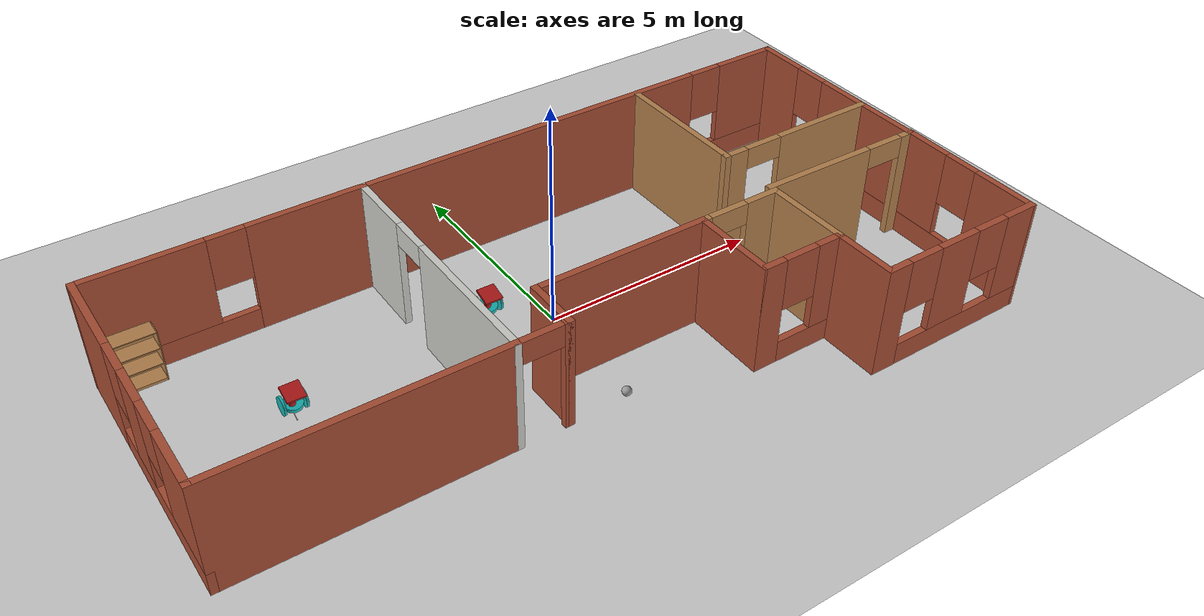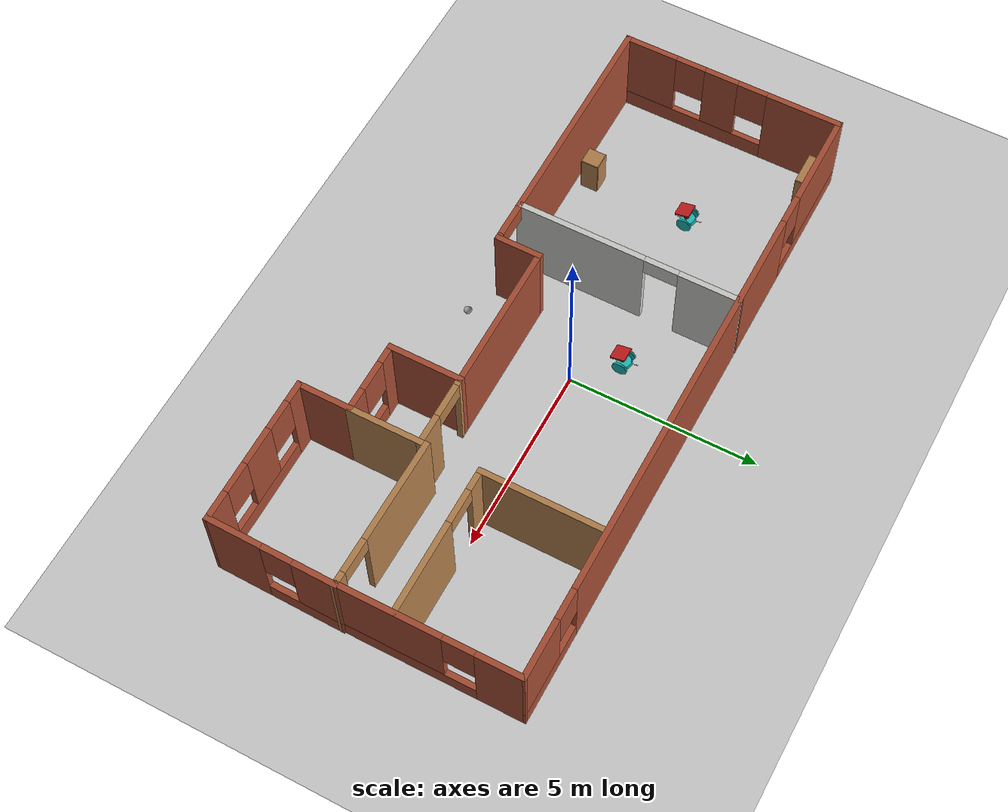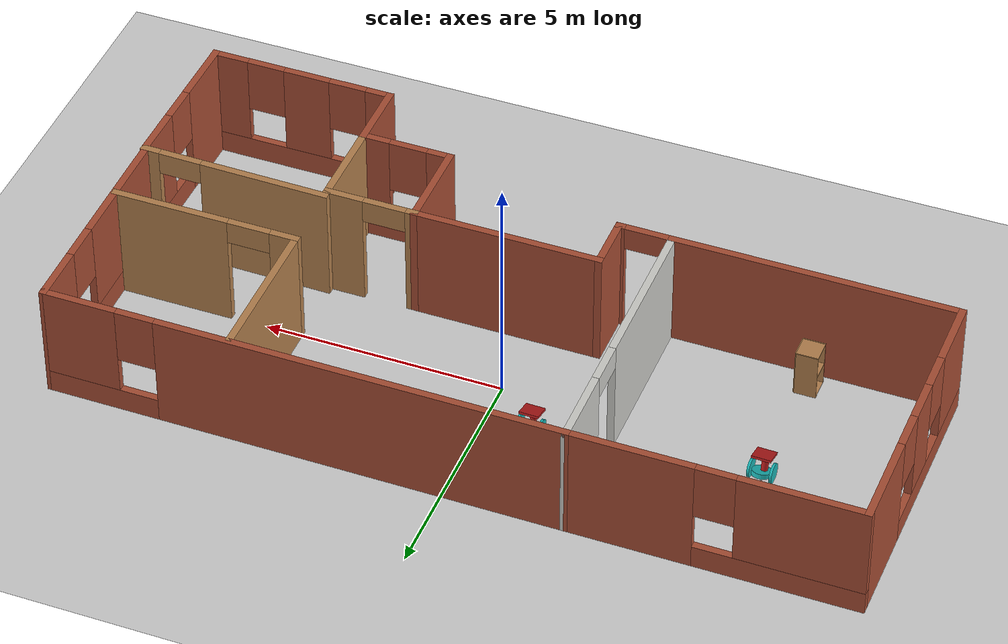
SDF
<sdf version="1.6">
 <world name="default">
  <plugin name="welcome_message" filename="libwelcome_message.so"/>
  <light name="sun" type="directional">
   <pose>0 0 10 0 -0 0</pose>
   <diffuse>0.8 0.8 0.8 1</diffuse>
   <specular>0.2 0.2 0.2 1</specular>
   <attenuation>
    <range>1000</range>
    <constant>0.9</constant>
    <linear>0.01</linear>
    <quadratic>0.001</quadratic>
   </attenuation>
   <direction>-0.5 0.1 -0.9</direction>
  </light>
  <model name="ground_plane">
   <static>1</static>
   <link name="link">
    <collision name="collision">
     <geometry><plane><normal>0 0 1</normal><size>100 100</size></plane></geometry>
     <surface><friction><ode><mu>100</mu><mu2>50</mu2></ode></friction></surface>
    </collision>
    <visual name="visual">
     <cast_shadows>0</cast_shadows>
     <geometry><plane><normal>0 0 1</normal><size>100 100</size></plane></geometry>
     <material>
      <script><uri>file://media/materials/scripts/gazebo.material</uri><name>Gazebo/Grey</name></script>
     </material>
    </visual>
   </link>
  </model>
  <gravity>0 0 -9.8</gravity>
  <magnetic_field>6e-06 2.3e-05 -4.2e-05</magnetic_field>
  <atmosphere type="adiabatic"/>
  <physics name="default_physics" default="0" type="ode">
   <max_step_size>0.001</max_step_size>
   <real_time_factor>1</real_time_factor>
   <real_time_update_rate>1000</real_time_update_rate>
  </physics>
  <scene><ambient>0.4 0.4 0.4 1</ambient><background>0.7 0.7 0.7 1</background><shadows>1</shadows></scene>
  <spherical_coordinates>
   <surface_model>EARTH_WGS84</surface_model>
   <latitude_deg>0</latitude_deg>
   <longitude_deg>0</longitude_deg>
   <elevation>0</elevation>
   <heading_deg>0</heading_deg>
  </spherical_coordinates>
  <model name="myhouse">
   <pose>-0.06085 -0.82016 0 0 -0 0</pose>
   <link name="Wall_0">
    <pose>-1.87765 -1.87448 0 0 -0 0</pose>
    <visual name="Wall_0_Visual_0">
     <pose>-0.555853 0 1.25 0 -0 0</pose>
     <geometry><box><size>0.138293 0.15 2.5</size></box></geometry>
     <material>
      <script><uri>file://media/materials/scripts/gazebo.material</uri><name>Gazebo/Bricks</name></script>
      <ambient>1 1 1 1</ambient>
     </material>
     <meta><layer>0</layer></meta>
    </visual>
    <collision name="Wall_0_Collision_0">
     <geometry><box><size>0.138293 0.15 2.5</size></box></geometry>
     <pose>-0.555853 0 1.25 0 -0 0</pose>
    </collision>
    <visual name="Wall_0_Visual_1">
     <pose>0.519147 0 1.25 0 -0 0</pose>
     <geometry><box><size>0.211707 0.15 2.5</size></box></geometry>
     <material>
      <script><uri>file://media/materials/scripts/gazebo.material</uri><name>Gazebo/Bricks</name></script>
      <ambient>1 1 1 1</ambient>
     </material>
     <meta><layer>0</layer></meta>
    </visual>
    <collision name="Wall_0_Collision_1">
     <geometry><box><size>0.211707 0.15 2.5</size></box></geometry>
     <pose>0.519147 0 1.25 0 -0 0</pose>
    </collision>
    <visual name="Wall_0_Visual_2">
     <pose>-0.036707 0 2.25 0 -0 0</pose>
     <geometry><box><size>0.9 0.15 0.5</size></box></geometry>
     <material>
      <script><uri>file://media/materials/scripts/gazebo.material</uri><name>Gazebo/Bricks</name></script>
      <ambient>1 1 1 1</ambient>
     </material>
     <meta><layer>0</layer></meta>
    </visual>
    <collision name="Wall_0_Collision_2">
     <geometry><box><size>0.9 0.15 0.5</size></box></geometry>
     <pose>-0.036707 0 2.25 0 -0 0</pose>
    </collision>
   </link>
   <link name="Wall_1">
    <collision name="Wall_1_Collision">
     <geometry><box><size>1.25 0.15 2.5</size></box></geometry>
     <pose>0 0 1.25 0 -0 0</pose>
    </collision>
    <visual name="Wall_1_Visual">
     <pose>0 0 1.25 0 -0 0</pose>
     <geometry><box><size>1.25 0.15 2.5</size></box></geometry>
     <material>
      <script><uri>file://media/materials/scripts/gazebo.material</uri><name>Gazebo/Bricks</name></script>
      <ambient>1 1 1 1</ambient>
     </material>
     <meta><layer>0</layer></meta>
    </visual>
    <pose>-1.32765 -1.32448 0 0 -0 1.5708</pose>
   </link>
   <link name="Wall_10">
    <pose>8.24939 -2.32652 0 0 -0 1.55439</pose>
    <visual name="Wall_10_Visual_0">
     <pose>-0.982609 0 1.25 0 -0 0</pose>
     <geometry><box><size>1.48115 0.15 2.5</size></box></geometry>
     <material>
      <script><uri>file://media/materials/scripts/gazebo.material</uri><name>Gazebo/Bricks</name></script>
      <ambient>1 1 1 1</ambient>
     </material>
     <meta><layer>0</layer></meta>
    </visual>
    <collision name="Wall_10_Collision_0">
     <geometry><box><size>1.48115 0.15 2.5</size></box></geometry>
     <pose>-0.982609 0 1.25 0 -0 0</pose>
    </collision>
    <visual name="Wall_10_Visual_1">
     <pose>0.740575 0 0.25 0 -0 0</pose>
     <geometry><box><size>1.96522 0.15 0.5</size></box></geometry>
     <material>
      <script><uri>file://media/materials/scripts/gazebo.material</uri><name>Gazebo/Bricks</name></script>
      <ambient>1 1 1 1</ambient>
     </material>
     <meta><layer>0</layer></meta>
    </visual>
    <collision name="Wall_10_Collision_1">
     <geometry><box><size>1.96522 0.15 0.5</size></box></geometry>
     <pose>0.740575 0 0.25 0 -0 0</pose>
    </collision>
    <visual name="Wall_10_Visual_2">
     <pose>1.14057 0 1.5 0 -0 0</pose>
     <geometry><box><size>1.16522 0.15 2</size></box></geometry>
     <material>
      <script><uri>file://media/materials/scripts/gazebo.material</uri><name>Gazebo/Bricks</name></script>
      <ambient>1 1 1 1</ambient>
     </material>
     <meta><layer>0</layer></meta>
    </visual>
    <collision name="Wall_10_Collision_2">
     <geometry><box><size>1.16522 0.15 2</size></box></geometry>
     <pose>1.14057 0 1.5 0 -0 0</pose>
    </collision>
    <visual name="Wall_10_Visual_3">
     <pose>0.157966 0 1.9 0 -0 0</pose>
     <geometry><box><size>0.8 0.15 1.2</size></box></geometry>
     <material>
      <script><uri>file://media/materials/scripts/gazebo.material</uri><name>Gazebo/Bricks</name></script>
      <ambient>1 1 1 1</ambient>
     </material>
     <meta><layer>0</layer></meta>
    </visual>
    <collision name="Wall_10_Collision_3">
     <geometry><box><size>0.8 0.15 1.2</size></box></geometry>
     <pose>0.157966 0 1.9 0 -0 0</pose>
    </collision>
   </link>
   <link name="Wall_12">
    <pose>6.32439 -0.651522 0 0 0 -0.01385</pose>
    <visual name="Wall_12_Visual_0">
     <pose>-0.654543 0 1.25 0 -0 0</pose>
     <geometry><box><size>2.74536 0.15 2.5</size></box></geometry>
     <material>
      <script><uri>file://media/materials/scripts/gazebo.material</uri><name>Gazebo/Wood</name></script>
      <ambient>1 1 1 1</ambient>
     </material>
     <meta><layer>0</layer></meta>
    </visual>
    <collision name="Wall_12_Collision_0">
     <geometry><box><size>2.74536 0.15 2.5</size></box></geometry>
     <pose>-0.654543 0 1.25 0 -0 0</pose>
    </collision>
    <visual name="Wall_12_Visual_1">
     <pose>1.82268 0 1.25 0 -0 0</pose>
     <geometry><box><size>0.409086 0.15 2.5</size></box></geometry>
     <material>
      <script><uri>file://media/materials/scripts/gazebo.material</uri><name>Gazebo/Wood</name></script>
      <ambient>1 1 1 1</ambient>
     </material>
     <meta><layer>0</layer></meta>
    </visual>
    <collision name="Wall_12_Collision_1">
     <geometry><box><size>0.409086 0.15 2.5</size></box></geometry>
     <pose>1.82268 0 1.25 0 -0 0</pose>
    </collision>
    <visual name="Wall_12_Visual_2">
     <pose>1.16814 0 2.25 0 -0 0</pose>
     <geometry><box><size>0.9 0.15 0.5</size></box></geometry>
     <material>
      <script><uri>file://media/materials/scripts/gazebo.material</uri><name>Gazebo/Wood</name></script>
      <ambient>1 1 1 1</ambient>
     </material>
     <meta><layer>0</layer></meta>
    </visual>
    <collision name="Wall_12_Collision_2">
     <geometry><box><size>0.9 0.15 0.5</size></box></geometry>
     <pose>1.16814 0 2.25 0 -0 0</pose>
    </collision>
   </link>
   <link name="Wall_14">
    <pose>-2.42765 1.05052 0 0 -0 1.5708</pose>
    <visual name="Wall_14_Visual_0">
     <pose>-1.27529 0 1.25 0 -0 0</pose>
     <geometry><box><size>3.44943 0.15 2.5</size></box></geometry>
     <material>
      <script><uri>file://media/materials/scripts/gazebo.material</uri><name>Gazebo/CeilingTiled</name></script>
      <ambient>1 1 0 1</ambient>
     </material>
     <meta><layer>0</layer></meta>
    </visual>
    <collision name="Wall_14_Collision_0">
     <geometry><box><size>3.44943 0.15 2.5</size></box></geometry>
     <pose>-1.27529 0 1.25 0 -0 0</pose>
    </collision>
    <visual name="Wall_14_Visual_1">
     <pose>2.17471 0 1.25 0 -0 0</pose>
     <geometry><box><size>1.65057 0.15 2.5</size></box></geometry>
     <material>
      <script><uri>file://media/materials/scripts/gazebo.material</uri><name>Gazebo/CeilingTiled</name></script>
      <ambient>1 1 0 1</ambient>
     </material>
     <meta><layer>0</layer></meta>
    </visual>
    <collision name="Wall_14_Collision_1">
     <geometry><box><size>1.65057 0.15 2.5</size></box></geometry>
     <pose>2.17471 0 1.25 0 -0 0</pose>
    </collision>
    <visual name="Wall_14_Visual_2">
     <pose>0.899425 0 2.25 0 -0 0</pose>
     <geometry><box><size>0.9 0.15 0.5</size></box></geometry>
     <material>
      <script><uri>file://media/materials/scripts/gazebo.material</uri><name>Gazebo/CeilingTiled</name></script>
      <ambient>1 1 0 1</ambient>
     </material>
     <meta><layer>0</layer></meta>
    </visual>
    <collision name="Wall_14_Collision_2">
     <geometry><box><size>0.9 0.15 0.5</size></box></geometry>
     <pose>0.899425 0 2.25 0 -0 0</pose>
    </collision>
   </link>
   <link name="Wall_15">
    <pose>-5.35265 3.97552 0 0 -0 3.14159</pose>
    <visual name="Wall_15_Visual_0">
     <pose>-1.69701 0 1.25 0 -0 0</pose>
     <geometry><box><size>2.60598 0.15 2.5</size></box></geometry>
     <material>
      <script><uri>file://media/materials/scripts/gazebo.material</uri><name>Gazebo/Bricks</name></script>
      <ambient>1 1 1 1</ambient>
     </material>
     <meta><layer>0</layer></meta>
    </visual>
    <collision name="Wall_15_Collision_0">
     <geometry><box><size>2.60598 0.15 2.5</size></box></geometry>
     <pose>-1.69701 0 1.25 0 -0 0</pose>
    </collision>
    <visual name="Wall_15_Visual_1">
     <pose>1.30299 0 0.25 0 -0 0</pose>
     <geometry><box><size>3.39402 0.15 0.5</size></box></geometry>
     <material>
      <script><uri>file://media/materials/scripts/gazebo.material</uri><name>Gazebo/Bricks</name></script>
      <ambient>1 1 1 1</ambient>
     </material>
     <meta><layer>0</layer></meta>
    </visual>
    <collision name="Wall_15_Collision_1">
     <geometry><box><size>3.39402 0.15 0.5</size></box></geometry>
     <pose>1.30299 0 0.25 0 -0 0</pose>
    </collision>
    <visual name="Wall_15_Visual_2">
     <pose>1.70299 0 1.5 0 -0 0</pose>
     <geometry><box><size>2.59402 0.15 2</size></box></geometry>
     <material>
      <script><uri>file://media/materials/scripts/gazebo.material</uri><name>Gazebo/Bricks</name></script>
      <ambient>1 1 1 1</ambient>
     </material>
     <meta><layer>0</layer></meta>
    </visual>
    <collision name="Wall_15_Collision_2">
     <geometry><box><size>2.59402 0.15 2</size></box></geometry>
     <pose>1.70299 0 1.5 0 -0 0</pose>
    </collision>
    <visual name="Wall_15_Visual_3">
     <pose>0.005982 0 1.9 0 -0 0</pose>
     <geometry><box><size>0.8 0.15 1.2</size></box></geometry>
     <material>
      <script><uri>file://media/materials/scripts/gazebo.material</uri><name>Gazebo/Bricks</name></script>
      <ambient>1 1 1 1</ambient>
     </material>
     <meta><layer>0</layer></meta>
    </visual>
    <collision name="Wall_15_Collision_3">
     <geometry><box><size>0.8 0.15 1.2</size></box></geometry>
     <pose>0.005982 0 1.9 0 -0 0</pose>
    </collision>
   </link>
   <link name="Wall_16">
    <pose>-8.27765 1.05052 0 0 0 -1.5708</pose>
    <visual name="Wall_16_Visual_0">
     <pose>-1.99021 0 1.25 0 -0 0</pose>
     <geometry><box><size>2.01957 0.15 2.5</size></box></geometry>
     <material>
      <script><uri>file://media/materials/scripts/gazebo.material</uri><name>Gazebo/Bricks</name></script>
      <ambient>1 1 1 1</ambient>
     </material>
     <meta><layer>0</layer></meta>
    </visual>
    <collision name="Wall_16_Collision_0">
     <geometry><box><size>2.01957 0.15 2.5</size></box></geometry>
     <pose>-1.99021 0 1.25 0 -0 0</pose>
    </collision>
    <visual name="Wall_16_Visual_1">
     <pose>1.00979 0 0.25 0 -0 0</pose>
     <geometry><box><size>3.98043 0.15 0.5</size></box></geometry>
     <material>
      <script><uri>file://media/materials/scripts/gazebo.material</uri><name>Gazebo/Bricks</name></script>
      <ambient>1 1 1 1</ambient>
     </material>
     <meta><layer>0</layer></meta>
    </visual>
    <collision name="Wall_16_Collision_1">
     <geometry><box><size>3.98043 0.15 0.5</size></box></geometry>
     <pose>1.00979 0 0.25 0 -0 0</pose>
    </collision>
    <visual name="Wall_16_Visual_2">
     <pose>0.277751 0 1.5 0 -0 0</pose>
     <geometry><box><size>0.916358 0.15 2</size></box></geometry>
     <material>
      <script><uri>file://media/materials/scripts/gazebo.material</uri><name>Gazebo/Bricks</name></script>
      <ambient>1 1 1 1</ambient>
     </material>
     <meta><layer>0</layer></meta>
    </visual>
    <collision name="Wall_16_Collision_2">
     <geometry><box><size>0.916358 0.15 2</size></box></geometry>
     <pose>0.277751 0 1.5 0 -0 0</pose>
    </collision>
    <visual name="Wall_16_Visual_3">
     <pose>2.26796 0 1.5 0 -0 0</pose>
     <geometry><box><size>1.46407 0.15 2</size></box></geometry>
     <material>
      <script><uri>file://media/materials/scripts/gazebo.material</uri><name>Gazebo/Bricks</name></script>
      <ambient>1 1 1 1</ambient>
     </material>
     <meta><layer>0</layer></meta>
    </visual>
    <collision name="Wall_16_Collision_3">
     <geometry><box><size>1.46407 0.15 2</size></box></geometry>
     <pose>2.26796 0 1.5 0 -0 0</pose>
    </collision>
    <visual name="Wall_16_Visual_4">
     <pose>-0.580428 0 1.9 0 -0 0</pose>
     <geometry><box><size>0.8 0.15 1.2</size></box></geometry>
     <material>
      <script><uri>file://media/materials/scripts/gazebo.material</uri><name>Gazebo/Bricks</name></script>
      <ambient>1 1 1 1</ambient>
     </material>
     <meta><layer>0</layer></meta>
    </visual>
    <collision name="Wall_16_Collision_4">
     <geometry><box><size>0.8 0.15 1.2</size></box></geometry>
     <pose>-0.580428 0 1.9 0 -0 0</pose>
    </collision>
    <visual name="Wall_16_Visual_5">
     <pose>1.13593 0 1.9 0 -0 0</pose>
     <geometry><box><size>0.8 0.15 1.2</size></box></geometry>
     <material>
      <script><uri>file://media/materials/scripts/gazebo.material</uri><name>Gazebo/Bricks</name></script>
      <ambient>1 1 1 1</ambient>
     </material>
     <meta><layer>0</layer></meta>
    </visual>
    <collision name="Wall_16_Collision_5">
     <geometry><box><size>0.8 0.15 1.2</size></box></geometry>
     <pose>1.13593 0 1.9 0 -0 0</pose>
    </collision>
   </link>
   <link name="Wall_17">
    <collision name="Wall_17_Collision">
     <geometry><box><size>6 0.15 2.5</size></box></geometry>
     <pose>0 0 1.25 0 -0 0</pose>
    </collision>
    <visual name="Wall_17_Visual">
     <pose>0 0 1.25 0 -0 0</pose>
     <geometry><box><size>6 0.15 2.5</size></box></geometry>
     <material>
      <script><uri>file://media/materials/scripts/gazebo.material</uri><name>Gazebo/Bricks</name></script>
      <ambient>1 1 1 1</ambient>
     </material>
     <meta><layer>0</layer></meta>
    </visual>
    <pose>-5.35265 -1.87448 0 0 -0 0</pose>
   </link>
   <link name="Wall_19">
    <pose>2.91087 3.962 0 0 0 -0.002532</pose>
    <visual name="Wall_19_Visual_0">
     <pose>-1.19531 0 1.25 0 -0 0</pose>
     <geometry><box><size>8.43646 0.15 2.5</size></box></geometry>
     <material>
      <script><uri>file://media/materials/scripts/gazebo.material</uri><name>Gazebo/Bricks</name></script>
      <ambient>1 1 1 1</ambient>
     </material>
     <meta><layer>0</layer></meta>
    </visual>
    <collision name="Wall_19_Collision_0">
     <geometry><box><size>8.43646 0.15 2.5</size></box></geometry>
     <pose>-1.19531 0 1.25 0 -0 0</pose>
    </collision>
    <visual name="Wall_19_Visual_1">
     <pose>4.21823 0 0.25 0 -0 0</pose>
     <geometry><box><size>2.39061 0.15 0.5</size></box></geometry>
     <material>
      <script><uri>file://media/materials/scripts/gazebo.material</uri><name>Gazebo/Bricks</name></script>
      <ambient>1 1 1 1</ambient>
     </material>
     <meta><layer>0</layer></meta>
    </visual>
    <collision name="Wall_19_Collision_1">
     <geometry><box><size>2.39061 0.15 0.5</size></box></geometry>
     <pose>4.21823 0 0.25 0 -0 0</pose>
    </collision>
    <visual name="Wall_19_Visual_2">
     <pose>4.61823 0 1.5 0 -0 0</pose>
     <geometry><box><size>1.59061 0.15 2</size></box></geometry>
     <material>
      <script><uri>file://media/materials/scripts/gazebo.material</uri><name>Gazebo/Bricks</name></script>
      <ambient>1 1 1 1</ambient>
     </material>
     <meta><layer>0</layer></meta>
    </visual>
    <collision name="Wall_19_Collision_2">
     <geometry><box><size>1.59061 0.15 2</size></box></geometry>
     <pose>4.61823 0 1.5 0 -0 0</pose>
    </collision>
    <visual name="Wall_19_Visual_3">
     <pose>3.42292 0 1.9 0 -0 0</pose>
     <geometry><box><size>0.8 0.15 1.2</size></box></geometry>
     <material>
      <script><uri>file://media/materials/scripts/gazebo.material</uri><name>Gazebo/Bricks</name></script>
      <ambient>1 1 1 1</ambient>
     </material>
     <meta><layer>0</layer></meta>
    </visual>
    <collision name="Wall_19_Collision_3">
     <geometry><box><size>0.8 0.15 1.2</size></box></geometry>
     <pose>3.42292 0 1.9 0 -0 0</pose>
    </collision>
   </link>
   <link name="Wall_2">
    <collision name="Wall_2_Collision">
     <geometry><box><size>4 0.15 2.5</size></box></geometry>
     <pose>0 0 1.25 0 -0 0</pose>
    </collision>
    <visual name="Wall_2_Visual">
     <pose>0 0 1.25 0 -0 0</pose>
     <geometry><box><size>4 0.15 2.5</size></box></geometry>
     <material>
      <script><uri>file://media/materials/scripts/gazebo.material</uri><name>Gazebo/Bricks</name></script>
      <ambient>1 1 1 1</ambient>
     </material>
     <meta><layer>0</layer></meta>
    </visual>
    <pose>0.597353 -0.774485 0 0 -0 0</pose>
   </link>
   <link name="Wall_21">
    <pose>8.24939 1.64848 0 0 0 -1.5708</pose>
    <visual name="Wall_21_Visual_0">
     <pose>-1.75419 0 1.25 0 -0 0</pose>
     <geometry><box><size>1.24163 0.15 2.5</size></box></geometry>
     <material>
      <script><uri>file://media/materials/scripts/gazebo.material</uri><name>Gazebo/Bricks</name></script>
      <ambient>1 1 1 1</ambient>
     </material>
     <meta><layer>0</layer></meta>
    </visual>
    <collision name="Wall_21_Collision_0">
     <geometry><box><size>1.24163 0.15 2.5</size></box></geometry>
     <pose>-1.75419 0 1.25 0 -0 0</pose>
    </collision>
    <visual name="Wall_21_Visual_1">
     <pose>0.620814 0 0.25 0 -0 0</pose>
     <geometry><box><size>3.50837 0.15 0.5</size></box></geometry>
     <material>
      <script><uri>file://media/materials/scripts/gazebo.material</uri><name>Gazebo/Bricks</name></script>
      <ambient>1 1 1 1</ambient>
     </material>
     <meta><layer>0</layer></meta>
    </visual>
    <collision name="Wall_21_Collision_1">
     <geometry><box><size>3.50837 0.15 0.5</size></box></geometry>
     <pose>0.620814 0 0.25 0 -0 0</pose>
    </collision>
    <visual name="Wall_21_Visual_2">
     <pose>1.02081 0 1.5 0 -0 0</pose>
     <geometry><box><size>2.70837 0.15 2</size></box></geometry>
     <material>
      <script><uri>file://media/materials/scripts/gazebo.material</uri><name>Gazebo/Bricks</name></script>
      <ambient>1 1 1 1</ambient>
     </material>
     <meta><layer>0</layer></meta>
    </visual>
    <collision name="Wall_21_Collision_2">
     <geometry><box><size>2.70837 0.15 2</size></box></geometry>
     <pose>1.02081 0 1.5 0 -0 0</pose>
    </collision>
    <visual name="Wall_21_Visual_3">
     <pose>-0.733373 0 1.9 0 -0 0</pose>
     <geometry><box><size>0.8 0.15 1.2</size></box></geometry>
     <material>
      <script><uri>file://media/materials/scripts/gazebo.material</uri><name>Gazebo/Bricks</name></script>
      <ambient>1 1 1 1</ambient>
     </material>
     <meta><layer>0</layer></meta>
    </visual>
    <collision name="Wall_21_Collision_3">
     <geometry><box><size>0.8 0.15 1.2</size></box></geometry>
     <pose>-0.733373 0 1.9 0 -0 0</pose>
    </collision>
   </link>
   <link name="Wall_23">
    <pose>6.30421 0.772765 0 0 -0 3.14159</pose>
    <visual name="Wall_23_Visual_0">
     <pose>-0.757202 0 1.25 0 -0 0</pose>
     <geometry><box><size>2.4856 0.15 2.5</size></box></geometry>
     <material>
      <script><uri>file://media/materials/scripts/gazebo.material</uri><name>Gazebo/Wood</name></script>
      <ambient>1 1 1 1</ambient>
     </material>
     <meta><layer>0</layer></meta>
    </visual>
    <collision name="Wall_23_Collision_0">
     <geometry><box><size>2.4856 0.15 2.5</size></box></geometry>
     <pose>-0.757202 0 1.25 0 -0 0</pose>
    </collision>
    <visual name="Wall_23_Visual_1">
     <pose>1.6928 0 1.25 0 -0 0</pose>
     <geometry><box><size>0.614403 0.15 2.5</size></box></geometry>
     <material>
      <script><uri>file://media/materials/scripts/gazebo.material</uri><name>Gazebo/Wood</name></script>
      <ambient>1 1 1 1</ambient>
     </material>
     <meta><layer>0</layer></meta>
    </visual>
    <collision name="Wall_23_Collision_1">
     <geometry><box><size>0.614403 0.15 2.5</size></box></geometry>
     <pose>1.6928 0 1.25 0 -0 0</pose>
    </collision>
    <visual name="Wall_23_Visual_2">
     <pose>0.935597 0 2.25 0 -0 0</pose>
     <geometry><box><size>0.9 0.15 0.5</size></box></geometry>
     <material>
      <script><uri>file://media/materials/scripts/gazebo.material</uri><name>Gazebo/Wood</name></script>
      <ambient>1 1 1 1</ambient>
     </material>
     <meta><layer>0</layer></meta>
    </visual>
    <collision name="Wall_23_Collision_2">
     <geometry><box><size>0.9 0.15 0.5</size></box></geometry>
     <pose>0.935597 0 2.25 0 -0 0</pose>
    </collision>
   </link>
   <link name="Wall_24">
    <collision name="Wall_24_Collision">
     <geometry><box><size>3.25 0.15 2.5</size></box></geometry>
     <pose>0 0 1.25 0 -0 0</pose>
    </collision>
    <visual name="Wall_24_Visual">
     <pose>0 0 1.25 0 -0 0</pose>
     <geometry><box><size>3.25 0.15 2.5</size></box></geometry>
     <material>
      <script><uri>file://media/materials/scripts/gazebo.material</uri><name>Gazebo/Wood</name></script>
      <ambient>0.921569 0.807843 0.615686 1</ambient>
     </material>
     <meta><layer>0</layer></meta>
    </visual>
    <pose>4.37921 2.32276 0 0 -0 1.5708</pose>
   </link>
   <link name="Wall_3">
    <collision name="Wall_3_Collision">
     <geometry><box><size>2 0.15 2.5</size></box></geometry>
     <pose>0 0 1.25 0 -0 0</pose>
    </collision>
    <visual name="Wall_3_Visual">
     <pose>0 0 1.25 0 -0 0</pose>
     <geometry><box><size>2 0.15 2.5</size></box></geometry>
     <material>
      <script><uri>file://media/materials/scripts/gazebo.material</uri><name>Gazebo/Bricks</name></script>
      <ambient>1 1 1 1</ambient>
     </material>
     <meta><layer>0</layer></meta>
    </visual>
    <pose>2.52235 -1.69948 0 0 0 -1.5708</pose>
   </link>
   <link name="Wall_4">
    <pose>3.44735 -2.62448 0 0 -0 0</pose>
    <visual name="Wall_4_Visual_0">
     <pose>-0.723076 0 1.25 0 -0 0</pose>
     <geometry><box><size>0.553849 0.15 2.5</size></box></geometry>
     <material>
      <script><uri>file://media/materials/scripts/gazebo.material</uri><name>Gazebo/Bricks</name></script>
      <ambient>1 1 1 1</ambient>
     </material>
     <meta><layer>0</layer></meta>
    </visual>
    <collision name="Wall_4_Collision_0">
     <geometry><box><size>0.553849 0.15 2.5</size></box></geometry>
     <pose>-0.723076 0 1.25 0 -0 0</pose>
    </collision>
    <visual name="Wall_4_Visual_1">
     <pose>0.276924 0 0.25 0 -0 0</pose>
     <geometry><box><size>1.44615 0.15 0.5</size></box></geometry>
     <material>
      <script><uri>file://media/materials/scripts/gazebo.material</uri><name>Gazebo/Bricks</name></script>
      <ambient>1 1 1 1</ambient>
     </material>
     <meta><layer>0</layer></meta>
    </visual>
    <collision name="Wall_4_Collision_1">
     <geometry><box><size>1.44615 0.15 0.5</size></box></geometry>
     <pose>0.276924 0 0.25 0 -0 0</pose>
    </collision>
    <visual name="Wall_4_Visual_2">
     <pose>0.676924 0 1.5 0 -0 0</pose>
     <geometry><box><size>0.646151 0.15 2</size></box></geometry>
     <material>
      <script><uri>file://media/materials/scripts/gazebo.material</uri><name>Gazebo/Bricks</name></script>
      <ambient>1 1 1 1</ambient>
     </material>
     <meta><layer>0</layer></meta>
    </visual>
    <collision name="Wall_4_Collision_2">
     <geometry><box><size>0.646151 0.15 2</size></box></geometry>
     <pose>0.676924 0 1.5 0 -0 0</pose>
    </collision>
    <visual name="Wall_4_Visual_3">
     <pose>-0.046151 0 1.9 0 -0 0</pose>
     <geometry><box><size>0.8 0.15 1.2</size></box></geometry>
     <material>
      <script><uri>file://media/materials/scripts/gazebo.material</uri><name>Gazebo/Bricks</name></script>
      <ambient>1 1 1 1</ambient>
     </material>
     <meta><layer>0</layer></meta>
    </visual>
    <collision name="Wall_4_Collision_3">
     <geometry><box><size>0.8 0.15 1.2</size></box></geometry>
     <pose>-0.046151 0 1.9 0 -0 0</pose>
    </collision>
   </link>
   <link name="Wall_5">
    <collision name="Wall_5_Collision">
     <geometry><box><size>2 0.15 2.5</size></box></geometry>
     <pose>0 0 1.25 0 -0 0</pose>
    </collision>
    <visual name="Wall_5_Visual">
     <pose>0 0 1.25 0 -0 0</pose>
     <geometry><box><size>2 0.15 2.5</size></box></geometry>
     <material>
      <script><uri>file://media/materials/scripts/gazebo.material</uri><name>Gazebo/Wood</name></script>
      <ambient>1 1 1 1</ambient>
     </material>
     <meta><layer>0</layer></meta>
    </visual>
    <pose>4.37235 -1.69948 0 0 -0 1.5708</pose>
   </link>
   <link name="Wall_6">
    <pose>3.44735 -0.774485 0 0 -0 3.14159</pose>
    <visual name="Wall_6_Visual_0">
     <pose>-0.577975 0 1.25 0 -0 0</pose>
     <geometry><box><size>0.84405 0.15 2.5</size></box></geometry>
     <material>
      <script><uri>file://media/materials/scripts/gazebo.material</uri><name>Gazebo/Wood</name></script>
      <ambient>0.435294 0.796078 0.67451 1</ambient>
     </material>
     <meta><layer>0</layer></meta>
    </visual>
    <collision name="Wall_6_Collision_0">
     <geometry><box><size>0.84405 0.15 2.5</size></box></geometry>
     <pose>-0.577975 0 1.25 0 -0 0</pose>
    </collision>
    <visual name="Wall_6_Visual_1">
     <pose>0.872025 0 1.25 0 -0 0</pose>
     <geometry><box><size>0.25595 0.15 2.5</size></box></geometry>
     <material>
      <script><uri>file://media/materials/scripts/gazebo.material</uri><name>Gazebo/Wood</name></script>
      <ambient>0.435294 0.796078 0.67451 1</ambient>
     </material>
     <meta><layer>0</layer></meta>
    </visual>
    <collision name="Wall_6_Collision_1">
     <geometry><box><size>0.25595 0.15 2.5</size></box></geometry>
     <pose>0.872025 0 1.25 0 -0 0</pose>
    </collision>
    <visual name="Wall_6_Visual_2">
     <pose>0.29405 0 2.25 0 -0 0</pose>
     <geometry><box><size>0.9 0.15 0.5</size></box></geometry>
     <material>
      <script><uri>file://media/materials/scripts/gazebo.material</uri><name>Gazebo/Wood</name></script>
      <ambient>0.435294 0.796078 0.67451 1</ambient>
     </material>
     <meta><layer>0</layer></meta>
    </visual>
    <collision name="Wall_6_Collision_2">
     <geometry><box><size>0.9 0.15 0.5</size></box></geometry>
     <pose>0.29405 0 2.25 0 -0 0</pose>
    </collision>
   </link>
   <link name="Wall_8">
    <collision name="Wall_8_Collision">
     <geometry><box><size>1.5 0.15 2.5</size></box></geometry>
     <pose>0 0 1.25 0 -0 0</pose>
    </collision>
    <visual name="Wall_8_Visual">
     <pose>0 0 1.25 0 -0 0</pose>
     <geometry><box><size>1.5 0.15 2.5</size></box></geometry>
     <material>
      <script><uri>file://media/materials/scripts/gazebo.material</uri><name>Gazebo/Bricks</name></script>
      <ambient>1 1 1 1</ambient>
     </material>
     <meta><layer>0</layer></meta>
    </visual>
    <pose>4.37235 -3.29948 0 0 0 -1.5708</pose>
   </link>
   <link name="Wall_9">
    <pose>6.29735 -3.97449 0 0 -0 0</pose>
    <visual name="Wall_9_Visual_0">
     <pose>-1.70763 0 1.25 0 -0 0</pose>
     <geometry><box><size>0.584738 0.15 2.5</size></box></geometry>
     <material>
      <script><uri>file://media/materials/scripts/gazebo.material</uri><name>Gazebo/Bricks</name></script>
      <ambient>1 1 1 1</ambient>
     </material>
     <meta><layer>0</layer></meta>
    </visual>
    <collision name="Wall_9_Collision_0">
     <geometry><box><size>0.584738 0.15 2.5</size></box></geometry>
     <pose>-1.70763 0 1.25 0 -0 0</pose>
    </collision>
    <visual name="Wall_9_Visual_1">
     <pose>0.292369 0 0.25 0 -0 0</pose>
     <geometry><box><size>3.41526 0.15 0.5</size></box></geometry>
     <material>
      <script><uri>file://media/materials/scripts/gazebo.material</uri><name>Gazebo/Bricks</name></script>
      <ambient>1 1 1 1</ambient>
     </material>
     <meta><layer>0</layer></meta>
    </visual>
    <collision name="Wall_9_Collision_1">
     <geometry><box><size>3.41526 0.15 0.5</size></box></geometry>
     <pose>0.292369 0 0.25 0 -0 0</pose>
    </collision>
    <visual name="Wall_9_Visual_2">
     <pose>-0.115707 0 1.5 0 -0 0</pose>
     <geometry><box><size>0.999111 0.15 2</size></box></geometry>
     <material>
      <script><uri>file://media/materials/scripts/gazebo.material</uri><name>Gazebo/Bricks</name></script>
      <ambient>1 1 1 1</ambient>
     </material>
     <meta><layer>0</layer></meta>
    </visual>
    <collision name="Wall_9_Collision_2">
     <geometry><box><size>0.999111 0.15 2</size></box></geometry>
     <pose>-0.115707 0 1.5 0 -0 0</pose>
    </collision>
    <visual name="Wall_9_Visual_3">
     <pose>1.59192 0 1.5 0 -0 0</pose>
     <geometry><box><size>0.816151 0.15 2</size></box></geometry>
     <material>
      <script><uri>file://media/materials/scripts/gazebo.material</uri><name>Gazebo/Bricks</name></script>
      <ambient>1 1 1 1</ambient>
     </material>
     <meta><layer>0</layer></meta>
    </visual>
    <collision name="Wall_9_Collision_3">
     <geometry><box><size>0.816151 0.15 2</size></box></geometry>
     <pose>1.59192 0 1.5 0 -0 0</pose>
    </collision>
    <visual name="Wall_9_Visual_4">
     <pose>-1.01526 0 1.9 0 -0 0</pose>
     <geometry><box><size>0.8 0.15 1.2</size></box></geometry>
     <material>
      <script><uri>file://media/materials/scripts/gazebo.material</uri><name>Gazebo/Bricks</name></script>
      <ambient>1 1 1 1</ambient>
     </material>
     <meta><layer>0</layer></meta>
    </visual>
    <collision name="Wall_9_Collision_4">
     <geometry><box><size>0.8 0.15 1.2</size></box></geometry>
     <pose>-1.01526 0 1.9 0 -0 0</pose>
    </collision>
    <visual name="Wall_9_Visual_5">
     <pose>0.783849 0 1.9 0 -0 0</pose>
     <geometry><box><size>0.8 0.15 1.2</size></box></geometry>
     <material>
      <script><uri>file://media/materials/scripts/gazebo.material</uri><name>Gazebo/Bricks</name></script>
      <ambient>1 1 1 1</ambient>
     </material>
     <meta><layer>0</layer></meta>
    </visual>
    <collision name="Wall_9_Collision_5">
     <geometry><box><size>0.8 0.15 1.2</size></box></geometry>
     <pose>0.783849 0 1.9 0 -0 0</pose>
    </collision>
   </link>
   <static>1</static>
  </model>
  <model name="bookshelf">
   <static>1</static>
   <link name="link">
    <inertial><mass>1</mass></inertial>
    <collision name="back">
     <pose>0 0.005 0.6 0 -0 0</pose>
     <geometry><box><size>0.9 0.01 1.2</size></box></geometry>
    </collision>
    <visual name="visual1">
     <pose>0 0.005 0.6 0 -0 0</pose>
     <geometry><box><size>0.9 0.01 1.2</size></box></geometry>
     <material>
      <script><uri>file://media/materials/scripts/gazebo.material</uri><name>Gazebo/Wood</name></script>
     </material>
    </visual>
    <collision name="left_side">
     <pose>0.45 -0.195 0.6 0 -0 0</pose>
     <geometry><box><size>0.02 0.4 1.2</size></box></geometry>
    </collision>
    <visual name="visual2">
     <pose>0.45 -0.195 0.6 0 -0 0</pose>
     <geometry><box><size>0.02 0.4 1.2</size></box></geometry>
     <material>
      <script><uri>file://media/materials/scripts/gazebo.material</uri><name>Gazebo/Wood</name></script>
     </material>
    </visual>
    <collision name="right_side">
     <pose>-0.45 -0.195 0.6 0 -0 0</pose>
     <geometry><box><size>0.02 0.4 1.2</size></box></geometry>
    </collision>
    <visual name="visual3">
     <pose>-0.45 -0.195 0.6 0 -0 0</pose>
     <geometry><box><size>0.02 0.4 1.2</size></box></geometry>
     <material>
      <script><uri>file://media/materials/scripts/gazebo.material</uri><name>Gazebo/Wood</name></script>
     </material>
    </visual>
    <collision name="bottom">
     <pose>0 -0.195 0.03 0 -0 0</pose>
     <geometry><box><size>0.88 0.4 0.06</size></box></geometry>
    </collision>
    <visual name="visual4">
     <pose>0 -0.195 0.03 0 -0 0</pose>
     <geometry><box><size>0.88 0.4 0.06</size></box></geometry>
     <material>
      <script><uri>file://media/materials/scripts/gazebo.material</uri><name>Gazebo/Wood</name></script>
     </material>
    </visual>
    <collision name="top">
     <pose>0 -0.195 1.19 0 -0 0</pose>
     <geometry><box><size>0.88 0.4 0.02</size></box></geometry>
    </collision>
    <visual name="visual5">
     <pose>0 -0.195 1.19 0 -0 0</pose>
     <geometry><box><size>0.88 0.4 0.02</size></box></geometry>
     <material>
      <script><uri>file://media/materials/scripts/gazebo.material</uri><name>Gazebo/Wood</name></script>
     </material>
    </visual>
    <collision name="low_shelf">
     <pose>0 -0.195 0.43 0 -0 0</pose>
     <geometry><box><size>0.88 0.4 0.02</size></box></geometry>
    </collision>
    <visual name="visual6">
     <pose>0 -0.195 0.43 0 -0 0</pose>
     <geometry><box><size>0.88 0.4 0.02</size></box></geometry>
     <material>
      <script><uri>file://media/materials/scripts/gazebo.material</uri><name>Gazebo/Wood</name></script>
     </material>
    </visual>
    <collision name="high_shelf">
     <pose>0 -0.195 0.8 0 -0 0</pose>
     <geometry><box><size>0.88 0.4 0.02</size></box></geometry>
    </collision>
    <visual name="visual7">
     <pose>0 -0.195 0.8 0 -0 0</pose>
     <geometry><box><size>0.88 0.4 0.02</size></box></geometry>
     <material>
      <script><uri>file://media/materials/scripts/gazebo.material</uri><name>Gazebo/Wood</name></script>
     </material>
    </visual>
   </link>
   <pose>-7.63263 3.03401 0 0 -0 0</pose>
  </model>
  <model name="cabinet">
   <static>1</static>
   <link name="cabinet_bottom_plate">
    <inertial>
     <pose>0 0 -1 0 -0 0</pose>
     <inertia><ixx>2.05</ixx><ixy>0</ixy><ixz>0</ixz><iyy>2.05</iyy><iyz>0</iyz><izz>2.05</izz></inertia>
     <mass>25</mass>
    </inertial>
    <collision name="cabinet_bottom_plate_geom">
     <pose>0 0 0.01 0 -0 0</pose>
     <geometry><box><size>0.45 0.45 0.02</size></box></geometry>
    </collision>
    <visual name="cabinet_bottom_plate_geom_visual">
     <pose>0 0 0.01 0 -0 0</pose>
     <geometry><box><size>0.45 0.45 0.02</size></box></geometry>
     <material>
      <script><uri>file://media/materials/scripts/gazebo.material</uri><name>Gazebo/Wood</name></script>
     </material>
    </visual>
    <collision name="cabinet_bottom_plate_geom_cabinet_back_plate">
     <pose>0.235 0 0.51 0 -0 0</pose>
     <geometry><box><size>0.02 0.45 1.02</size></box></geometry>
    </collision>
    <visual name="cabinet_bottom_plate_geom_cabinet_back_plate_visual">
     <pose>0.235 0 0.51 0 -0 0</pose>
     <geometry><box><size>0.02 0.45 1.02</size></box></geometry>
     <material>
      <script><uri>file://media/materials/scripts/gazebo.material</uri><name>Gazebo/Wood</name></script>
     </material>
    </visual>
    <collision name="cabinet_bottom_plate_geom_cabinet_left_plate">
     <pose>0 0.235 0.51 0 -0 0</pose>
     <geometry><box><size>0.45 0.02 1.02</size></box></geometry>
    </collision>
    <visual name="cabinet_bottom_plate_geom_cabinet_left_plate_visual">
     <pose>0 0.235 0.51 0 -0 0</pose>
     <geometry><box><size>0.45 0.02 1.02</size></box></geometry>
     <material>
      <script><uri>file://media/materials/scripts/gazebo.material</uri><name>Gazebo/Wood</name></script>
     </material>
    </visual>
    <collision name="cabinet_bottom_plate_geom_cabinet_middle_plate">
     <pose>0 0 0.51 0 -0 0</pose>
     <geometry><box><size>0.45 0.45 0.02</size></box></geometry>
    </collision>
    <visual name="cabinet_bottom_plate_geom_cabinet_middle_plate_visual">
     <pose>0 0 0.51 0 -0 0</pose>
     <geometry><box><size>0.45 0.45 0.02</size></box></geometry>
     <material>
      <script><uri>file://media/materials/scripts/gazebo.material</uri><name>Gazebo/Wood</name></script>
     </material>
    </visual>
    <collision name="cabinet_bottom_plate_geom_cabinet_right_plate">
     <pose>0 -0.235 0.51 0 -0 0</pose>
     <geometry><box><size>0.45 0.02 1.02</size></box></geometry>
    </collision>
    <visual name="cabinet_bottom_plate_geom_cabinet_right_plate_visual">
     <pose>0 -0.235 0.51 0 -0 0</pose>
     <geometry><box><size>0.45 0.02 1.02</size></box></geometry>
     <material>
      <script><uri>file://media/materials/scripts/gazebo.material</uri><name>Gazebo/Wood</name></script>
     </material>
    </visual>
    <collision name="cabinet_bottom_plate_geom_cabinet_top_plate">
     <pose>0 0 1.01 0 -0 0</pose>
     <geometry><box><size>0.45 0.45 0.02</size></box></geometry>
    </collision>
    <visual name="cabinet_bottom_plate_geom_cabinet_top_plate_visual">
     <pose>0 0 1.01 0 -0 0</pose>
     <geometry><box><size>0.45 0.45 0.02</size></box></geometry>
     <material>
      <script><uri>file://media/materials/scripts/gazebo.material</uri><name>Gazebo/Wood</name></script>
     </material>
    </visual>
   </link>
   <pose>-5.54527 -2.22271 0 0 -0 0</pose>
  </model>
  <model name="circlebot">
   <link name="link_0">
    <pose>1.06129 -0.214025 0.27147 0 -0 0</pose>
    <inertial>
     <mass>1</mass>
     <inertia><ixx>0.145833</ixx><ixy>0</ixy><ixz>0</ixz><iyy>0.145833</iyy><iyz>0</iyz><izz>0.125</izz></inertia>
    </inertial>
    <visual name="visual">
     <geometry><cylinder><radius>0.2</radius><length>0.1</length></cylinder></geometry>
     <material>
      <lighting>1</lighting>
      <script><uri>file://media/materials/scripts/gazebo.material</uri><name>Gazebo/Grey</name></script>
      <shader type="pixel"><normal_map>__default__</normal_map></shader>
      <ambient>0.3 0.7 0.7 1</ambient>
      <diffuse>0.1 0.7 0.7 1</diffuse>
      <specular>0.01 0.01 0.01 1</specular>
      <emissive>0 0 0 1</emissive>
     </material>
    </visual>
    <collision name="collision">
     <geometry><cylinder><radius>0.2</radius><length>0.1</length></cylinder></geometry>
     <surface>
      <friction>
       <ode><mu>1</mu><mu2>1</mu2><fdir1>0 0 0</fdir1><slip1>0</slip1><slip2>0</slip2></ode>
       <torsional>
        <coefficient>1</coefficient>
        <patch_radius>0</patch_radius>
        <surface_radius>0</surface_radius>
        <use_patch_radius>1</use_patch_radius>
        <ode><slip>0</slip></ode>
       </torsional>
      </friction>
      <bounce><restitution_coefficient>0</restitution_coefficient><threshold>1e+06</threshold></bounce>
      <contact>
       <collide_without_contact>0</collide_without_contact>
       <collide_without_contact_bitmask>1</collide_without_contact_bitmask>
       <collide_bitmask>1</collide_bitmask>
       <ode>
        <soft_cfm>0</soft_cfm>
        <soft_erp>0.2</soft_erp>
        <kp>1e+13</kp>
        <kd>1</kd>
        <max_vel>0.01</max_vel>
        <min_depth>0</min_depth>
       </ode>
       <bullet>
        <split_impulse>1</split_impulse>
        <split_impulse_penetration_threshold>-0.01</split_impulse_penetration_threshold>
        <soft_cfm>0</soft_cfm>
        <soft_erp>0.2</soft_erp>
        <kp>1e+13</kp>
        <kd>1</kd>
       </bullet>
      </contact>
     </surface>
    </collision>
   </link>
   <link name="link_0_0">
    <pose>0.993988 -0.214025 0.213031 -1.5708 0.010835 3e-06</pose>
    <inertial>
     <mass>1</mass>
     <inertia>
      <ixx>0.166667</ixx>
      <ixy>0</ixy>
      <ixz>0</ixz>
      <iyy>0.166667</iyy>
      <iyz>0</iyz>
      <izz>0.166667</izz>
     </inertia>
    </inertial>
    <visual name="visual">
     <geometry><box><size>0.01 0.01 0.7</size></box></geometry>
     <material>
      <lighting>1</lighting>
      <script><uri>file://media/materials/scripts/gazebo.material</uri><name>Gazebo/Grey</name></script>
      <shader type="pixel"><normal_map>__default__</normal_map></shader>
      <ambient>0.3 0.3 0.3 1</ambient>
      <diffuse>0.7 0.7 0.7 1</diffuse>
      <specular>0.01 0.01 0.01 1</specular>
      <emissive>0 0 0 1</emissive>
     </material>
    </visual>
    <collision name="collision">
     <geometry><box><size>0.01 0.01 0.7</size></box></geometry>
     <surface>
      <friction>
       <ode><mu>1</mu><mu2>1</mu2><fdir1>0 0 0</fdir1><slip1>0</slip1><slip2>0</slip2></ode>
       <torsional>
        <coefficient>1</coefficient>
        <patch_radius>0</patch_radius>
        <surface_radius>0</surface_radius>
        <use_patch_radius>1</use_patch_radius>
        <ode><slip>0</slip></ode>
       </torsional>
      </friction>
      <bounce><restitution_coefficient>0</restitution_coefficient><threshold>1e+06</threshold></bounce>
      <contact>
       <collide_without_contact>0</collide_without_contact>
       <collide_without_contact_bitmask>1</collide_without_contact_bitmask>
       <collide_bitmask>1</collide_bitmask>
       <ode>
        <soft_cfm>0</soft_cfm>
        <soft_erp>0.2</soft_erp>
        <kp>1e+13</kp>
        <kd>1</kd>
        <max_vel>0.01</max_vel>
        <min_depth>0</min_depth>
       </ode>
       <bullet>
        <split_impulse>1</split_impulse>
        <split_impulse_penetration_threshold>-0.01</split_impulse_penetration_threshold>
        <soft_cfm>0</soft_cfm>
        <soft_erp>0.2</soft_erp>
        <kp>1e+13</kp>
        <kd>1</kd>
       </bullet>
      </contact>
     </surface>
    </collision>
   </link>
   <link name="link_2">
    <pose>1.28631 -0.214025 0.316464 -0.000138 1.5707 -0.000138</pose>
    <inertial>
     <mass>1</mass>
     <inertia><ixx>0.145833</ixx><ixy>0</ixy><ixz>0</ixz><iyy>0.145833</iyy><iyz>0</iyz><izz>0.125</izz></inertia>
    </inertial>
    <visual name="visual">
     <geometry><cylinder><radius>0.2</radius><length>0.05</length></cylinder></geometry>
     <material>
      <lighting>1</lighting>
      <script><uri>file://media/materials/scripts/gazebo.material</uri><name>Gazebo/Grey</name></script>
      <shader type="pixel"><normal_map>__default__</normal_map></shader>
      <ambient>0.3 0.7 0.7 1</ambient>
      <diffuse>0.1 0.7 0.7 1</diffuse>
      <specular>0.01 0.01 0.01 1</specular>
      <emissive>0 0 0 1</emissive>
     </material>
    </visual>
    <collision name="collision">
     <geometry><cylinder><radius>0.2</radius><length>0.05</length></cylinder></geometry>
     <surface>
      <friction>
       <ode><mu>1</mu><mu2>1</mu2><fdir1>0 0 0</fdir1><slip1>0</slip1><slip2>0</slip2></ode>
       <torsional>
        <coefficient>1</coefficient>
        <patch_radius>0</patch_radius>
        <surface_radius>0</surface_radius>
        <use_patch_radius>1</use_patch_radius>
        <ode><slip>0</slip></ode>
       </torsional>
      </friction>
      <bounce><restitution_coefficient>0</restitution_coefficient><threshold>1e+06</threshold></bounce>
      <contact>
       <collide_without_contact>0</collide_without_contact>
       <collide_without_contact_bitmask>1</collide_without_contact_bitmask>
       <collide_bitmask>1</collide_bitmask>
       <ode>
        <soft_cfm>0</soft_cfm>
        <soft_erp>0.2</soft_erp>
        <kp>1e+13</kp>
        <kd>1</kd>
        <max_vel>0.01</max_vel>
        <min_depth>0</min_depth>
       </ode>
       <bullet>
        <split_impulse>1</split_impulse>
        <split_impulse_penetration_threshold>-0.01</split_impulse_penetration_threshold>
        <soft_cfm>0</soft_cfm>
        <soft_erp>0.2</soft_erp>
        <kp>1e+13</kp>
        <kd>1</kd>
       </bullet>
      </contact>
     </surface>
    </collision>
   </link>
   <link name="link_2_clone">
    <pose>0.836287 -0.214025 0.31647 -0.000138 1.5707 -0.000138</pose>
    <inertial>
     <mass>1</mass>
     <inertia><ixx>0.145833</ixx><ixy>0</ixy><ixz>0</ixz><iyy>0.145833</iyy><iyz>0</iyz><izz>0.125</izz></inertia>
    </inertial>
    <visual name="visual">
     <geometry><cylinder><radius>0.2</radius><length>0.05</length></cylinder></geometry>
     <material>
      <lighting>1</lighting>
      <script><uri>file://media/materials/scripts/gazebo.material</uri><name>Gazebo/Grey</name></script>
      <shader type="pixel"><normal_map>__default__</normal_map></shader>
      <ambient>0.3 0.7 0.7 1</ambient>
      <diffuse>0.1 0.7 0.7 1</diffuse>
      <specular>0.01 0.01 0.01 1</specular>
      <emissive>0 0 0 1</emissive>
     </material>
    </visual>
    <collision name="collision">
     <geometry><cylinder><radius>0.2</radius><length>0.05</length></cylinder></geometry>
     <surface>
      <friction>
       <ode><mu>1</mu><mu2>1</mu2><fdir1>0 0 0</fdir1><slip1>0</slip1><slip2>0</slip2></ode>
       <torsional>
        <coefficient>1</coefficient>
        <patch_radius>0</patch_radius>
        <surface_radius>0</surface_radius>
        <use_patch_radius>1</use_patch_radius>
        <ode><slip>0</slip></ode>
       </torsional>
      </friction>
      <bounce><restitution_coefficient>0</restitution_coefficient><threshold>1e+06</threshold></bounce>
      <contact>
       <collide_without_contact>0</collide_without_contact>
       <collide_without_contact_bitmask>1</collide_without_contact_bitmask>
       <collide_bitmask>1</collide_bitmask>
       <ode>
        <soft_cfm>0</soft_cfm>
        <soft_erp>0.2</soft_erp>
        <kp>1e+13</kp>
        <kd>1</kd>
        <max_vel>0.01</max_vel>
        <min_depth>0</min_depth>
       </ode>
       <bullet>
        <split_impulse>1</split_impulse>
        <split_impulse_penetration_threshold>-0.01</split_impulse_penetration_threshold>
        <soft_cfm>0</soft_cfm>
        <soft_erp>0.2</soft_erp>
        <kp>1e+13</kp>
        <kd>1</kd>
       </bullet>
      </contact>
     </surface>
    </collision>
   </link>
   <link name="link_3">
    <pose>1.02629 -0.249025 0.42147 0 -0 0</pose>
    <inertial>
     <mass>1</mass>
     <inertia><ixx>0.145833</ixx><ixy>0</ixy><ixz>0</ixz><iyy>0.145833</iyy><iyz>0</iyz><izz>0.125</izz></inertia>
    </inertial>
    <visual name="visual">
     <geometry><cylinder><radius>0.07</radius><length>0.4</length></cylinder></geometry>
     <material>
      <lighting>1</lighting>
      <script><uri>file://media/materials/scripts/gazebo.material</uri><name>Gazebo/Grey</name></script>
      <shader type="pixel"><normal_map>__default__</normal_map></shader>
      <ambient>0.7 0.1 0.1 1</ambient>
      <diffuse>0.7 0.1 0.1 1</diffuse>
      <specular>0.01 0.01 0.01 1</specular>
      <emissive>0 0 0 1</emissive>
     </material>
    </visual>
    <collision name="collision">
     <geometry><cylinder><radius>0.07</radius><length>0.4</length></cylinder></geometry>
     <surface>
      <friction>
       <ode><mu>1</mu><mu2>1</mu2><fdir1>0 0 0</fdir1><slip1>0</slip1><slip2>0</slip2></ode>
       <torsional>
        <coefficient>1</coefficient>
        <patch_radius>0</patch_radius>
        <surface_radius>0</surface_radius>
        <use_patch_radius>1</use_patch_radius>
        <ode><slip>0</slip></ode>
       </torsional>
      </friction>
      <bounce><restitution_coefficient>0</restitution_coefficient><threshold>1e+06</threshold></bounce>
      <contact>
       <collide_without_contact>0</collide_without_contact>
       <collide_without_contact_bitmask>1</collide_without_contact_bitmask>
       <collide_bitmask>1</collide_bitmask>
       <ode>
        <soft_cfm>0</soft_cfm>
        <soft_erp>0.2</soft_erp>
        <kp>1e+13</kp>
        <kd>1</kd>
        <max_vel>0.01</max_vel>
        <min_depth>0</min_depth>
       </ode>
       <bullet>
        <split_impulse>1</split_impulse>
        <split_impulse_penetration_threshold>-0.01</split_impulse_penetration_threshold>
        <soft_cfm>0</soft_cfm>
        <soft_erp>0.2</soft_erp>
        <kp>1e+13</kp>
        <kd>1</kd>
       </bullet>
      </contact>
     </surface>
    </collision>
   </link>
   <link name="link_4">
    <pose>1.06129 -0.214025 0.64647 0 -0 0</pose>
    <inertial>
     <mass>1</mass>
     <inertia>
      <ixx>0.166667</ixx>
      <ixy>0</ixy>
      <ixz>0</ixz>
      <iyy>0.166667</iyy>
      <iyz>0</iyz>
      <izz>0.166667</izz>
     </inertia>
    </inertial>
    <visual name="visual">
     <geometry><box><size>0.4 0.4 0.05</size></box></geometry>
     <material>
      <lighting>1</lighting>
      <script><uri>file://media/materials/scripts/gazebo.material</uri><name>Gazebo/Grey</name></script>
      <shader type="pixel"><normal_map>__default__</normal_map></shader>
      <ambient>0.7 0.1 0.1 1</ambient>
      <diffuse>0.7 0.1 0.1 1</diffuse>
      <specular>0.01 0.01 0.01 1</specular>
      <emissive>0 0 0 1</emissive>
     </material>
    </visual>
    <collision name="collision">
     <geometry><box><size>0.4 0.4 0.05</size></box></geometry>
     <surface>
      <friction>
       <ode><mu>1</mu><mu2>1</mu2><fdir1>0 0 0</fdir1><slip1>0</slip1><slip2>0</slip2></ode>
       <torsional>
        <coefficient>1</coefficient>
        <patch_radius>0</patch_radius>
        <surface_radius>0</surface_radius>
        <use_patch_radius>1</use_patch_radius>
        <ode><slip>0</slip></ode>
       </torsional>
      </friction>
      <bounce><restitution_coefficient>0</restitution_coefficient><threshold>1e+06</threshold></bounce>
      <contact>
       <collide_without_contact>0</collide_without_contact>
       <collide_without_contact_bitmask>1</collide_without_contact_bitmask>
       <collide_bitmask>1</collide_bitmask>
       <ode>
        <soft_cfm>0</soft_cfm>
        <soft_erp>0.2</soft_erp>
        <kp>1e+13</kp>
        <kd>1</kd>
        <max_vel>0.01</max_vel>
        <min_depth>0</min_depth>
       </ode>
       <bullet>
        <split_impulse>1</split_impulse>
        <split_impulse_penetration_threshold>-0.01</split_impulse_penetration_threshold>
        <soft_cfm>0</soft_cfm>
        <soft_erp>0.2</soft_erp>
        <kp>1e+13</kp>
        <kd>1</kd>
       </bullet>
      </contact>
     </surface>
    </collision>
   </link>
   <joint name="link_0_JOINT_0_0" type="fixed">
    <parent>link_0</parent>
    <child>link_0_0</child>
    <physics>
     <ode><limit><cfm>0</cfm><erp>0.2</erp></limit><suspension><cfm>0</cfm><erp>0.2</erp></suspension></ode>
    </physics>
   </joint>
   <joint name="link_0_JOINT_0" type="revolute">
    <parent>link_0</parent>
    <child>link_2_clone</child>
    <axis>
     <xyz>0 0 1</xyz>
     <use_parent_model_frame>0</use_parent_model_frame>
     <limit>
      <lower>-1.79769e+308</lower>
      <upper>1.79769e+308</upper>
      <effort>-1</effort>
      <velocity>-1</velocity>
     </limit>
     <dynamics>
      <spring_reference>0</spring_reference>
      <spring_stiffness>0</spring_stiffness>
      <damping>0</damping>
      <friction>0</friction>
     </dynamics>
    </axis>
    <physics>
     <ode><limit><cfm>0</cfm><erp>0.2</erp></limit><suspension><cfm>0</cfm><erp>0.2</erp></suspension></ode>
    </physics>
   </joint>
   <joint name="link_0_JOINT_1" type="revolute">
    <parent>link_0</parent>
    <child>link_2</child>
    <axis>
     <xyz>0 0 1</xyz>
     <use_parent_model_frame>0</use_parent_model_frame>
     <limit>
      <lower>-1.79769e+308</lower>
      <upper>1.79769e+308</upper>
      <effort>-1</effort>
      <velocity>-1</velocity>
     </limit>
     <dynamics>
      <spring_reference>0</spring_reference>
      <spring_stiffness>0</spring_stiffness>
      <damping>0</damping>
      <friction>0</friction>
     </dynamics>
    </axis>
    <physics>
     <ode><limit><cfm>0</cfm><erp>0.2</erp></limit><suspension><cfm>0</cfm><erp>0.2</erp></suspension></ode>
    </physics>
   </joint>
   <joint name="link_0_JOINT_2" type="fixed">
    <parent>link_0</parent>
    <child>link_3</child>
    <physics>
     <ode><limit><cfm>0</cfm><erp>0.2</erp></limit><suspension><cfm>0</cfm><erp>0.2</erp></suspension></ode>
    </physics>
   </joint>
   <joint name="link_3_JOINT_3" type="fixed">
    <parent>link_3</parent>
    <child>link_4</child>
    <physics>
     <ode><limit><cfm>0</cfm><erp>0.2</erp></limit><suspension><cfm>0</cfm><erp>0.2</erp></suspension></ode>
    </physics>
   </joint>
   <static>0</static>
   <pose>-6.55969 0.819403 -0.045944 0.276784 -8e-06 -0.016892</pose>
  </model>
  <model name="circlebot_0">
   <link name="link_0">
    <pose>1.06129 -0.214025 0.27147 0 -0 0</pose>
    <inertial>
     <mass>1</mass>
     <inertia><ixx>0.145833</ixx><ixy>0</ixy><ixz>0</ixz><iyy>0.145833</iyy><iyz>0</iyz><izz>0.125</izz></inertia>
    </inertial>
    <visual name="visual">
     <geometry><cylinder><radius>0.2</radius><length>0.1</length></cylinder></geometry>
     <material>
      <lighting>1</lighting>
      <script><uri>file://media/materials/scripts/gazebo.material</uri><name>Gazebo/Grey</name></script>
      <shader type="pixel"><normal_map>__default__</normal_map></shader>
      <ambient>0.3 0.7 0.7 1</ambient>
      <diffuse>0.1 0.7 0.7 1</diffuse>
      <specular>0.01 0.01 0.01 1</specular>
      <emissive>0 0 0 1</emissive>
     </material>
    </visual>
    <collision name="collision">
     <geometry><cylinder><radius>0.2</radius><length>0.1</length></cylinder></geometry>
     <surface>
      <friction>
       <ode><mu>1</mu><mu2>1</mu2><fdir1>0 0 0</fdir1><slip1>0</slip1><slip2>0</slip2></ode>
       <torsional>
        <coefficient>1</coefficient>
        <patch_radius>0</patch_radius>
        <surface_radius>0</surface_radius>
        <use_patch_radius>1</use_patch_radius>
        <ode><slip>0</slip></ode>
       </torsional>
      </friction>
      <bounce><restitution_coefficient>0</restitution_coefficient><threshold>1e+06</threshold></bounce>
      <contact>
       <collide_without_contact>0</collide_without_contact>
       <collide_without_contact_bitmask>1</collide_without_contact_bitmask>
       <collide_bitmask>1</collide_bitmask>
       <ode>
        <soft_cfm>0</soft_cfm>
        <soft_erp>0.2</soft_erp>
        <kp>1e+13</kp>
        <kd>1</kd>
        <max_vel>0.01</max_vel>
        <min_depth>0</min_depth>
       </ode>
       <bullet>
        <split_impulse>1</split_impulse>
        <split_impulse_penetration_threshold>-0.01</split_impulse_penetration_threshold>
        <soft_cfm>0</soft_cfm>
        <soft_erp>0.2</soft_erp>
        <kp>1e+13</kp>
        <kd>1</kd>
       </bullet>
      </contact>
     </surface>
    </collision>
   </link>
   <link name="link_0_0">
    <pose>0.993988 -0.214025 0.213031 -1.5708 0.010835 3e-06</pose>
    <inertial>
     <mass>1</mass>
     <inertia>
      <ixx>0.166667</ixx>
      <ixy>0</ixy>
      <ixz>0</ixz>
      <iyy>0.166667</iyy>
      <iyz>0</iyz>
      <izz>0.166667</izz>
     </inertia>
    </inertial>
    <visual name="visual">
     <geometry><box><size>0.01 0.01 0.7</size></box></geometry>
     <material>
      <lighting>1</lighting>
      <script><uri>file://media/materials/scripts/gazebo.material</uri><name>Gazebo/Grey</name></script>
      <shader type="pixel"><normal_map>__default__</normal_map></shader>
      <ambient>0.3 0.3 0.3 1</ambient>
      <diffuse>0.7 0.7 0.7 1</diffuse>
      <specular>0.01 0.01 0.01 1</specular>
      <emissive>0 0 0 1</emissive>
     </material>
    </visual>
    <collision name="collision">
     <geometry><box><size>0.01 0.01 0.7</size></box></geometry>
     <surface>
      <friction>
       <ode><mu>1</mu><mu2>1</mu2><fdir1>0 0 0</fdir1><slip1>0</slip1><slip2>0</slip2></ode>
       <torsional>
        <coefficient>1</coefficient>
        <patch_radius>0</patch_radius>
        <surface_radius>0</surface_radius>
        <use_patch_radius>1</use_patch_radius>
        <ode><slip>0</slip></ode>
       </torsional>
      </friction>
      <bounce><restitution_coefficient>0</restitution_coefficient><threshold>1e+06</threshold></bounce>
      <contact>
       <collide_without_contact>0</collide_without_contact>
       <collide_without_contact_bitmask>1</collide_without_contact_bitmask>
       <collide_bitmask>1</collide_bitmask>
       <ode>
        <soft_cfm>0</soft_cfm>
        <soft_erp>0.2</soft_erp>
        <kp>1e+13</kp>
        <kd>1</kd>
        <max_vel>0.01</max_vel>
        <min_depth>0</min_depth>
       </ode>
       <bullet>
        <split_impulse>1</split_impulse>
        <split_impulse_penetration_threshold>-0.01</split_impulse_penetration_threshold>
        <soft_cfm>0</soft_cfm>
        <soft_erp>0.2</soft_erp>
        <kp>1e+13</kp>
        <kd>1</kd>
       </bullet>
      </contact>
     </surface>
    </collision>
   </link>
   <link name="link_2">
    <pose>1.28631 -0.214025 0.316464 -0.000138 1.5707 -0.000138</pose>
    <inertial>
     <mass>1</mass>
     <inertia><ixx>0.145833</ixx><ixy>0</ixy><ixz>0</ixz><iyy>0.145833</iyy><iyz>0</iyz><izz>0.125</izz></inertia>
    </inertial>
    <visual name="visual">
     <geometry><cylinder><radius>0.2</radius><length>0.05</length></cylinder></geometry>
     <material>
      <lighting>1</lighting>
      <script><uri>file://media/materials/scripts/gazebo.material</uri><name>Gazebo/Grey</name></script>
      <shader type="pixel"><normal_map>__default__</normal_map></shader>
      <ambient>0.3 0.7 0.7 1</ambient>
      <diffuse>0.1 0.7 0.7 1</diffuse>
      <specular>0.01 0.01 0.01 1</specular>
      <emissive>0 0 0 1</emissive>
     </material>
    </visual>
    <collision name="collision">
     <geometry><cylinder><radius>0.2</radius><length>0.05</length></cylinder></geometry>
     <surface>
      <friction>
       <ode><mu>1</mu><mu2>1</mu2><fdir1>0 0 0</fdir1><slip1>0</slip1><slip2>0</slip2></ode>
       <torsional>
        <coefficient>1</coefficient>
        <patch_radius>0</patch_radius>
        <surface_radius>0</surface_radius>
        <use_patch_radius>1</use_patch_radius>
        <ode><slip>0</slip></ode>
       </torsional>
      </friction>
      <bounce><restitution_coefficient>0</restitution_coefficient><threshold>1e+06</threshold></bounce>
      <contact>
       <collide_without_contact>0</collide_without_contact>
       <collide_without_contact_bitmask>1</collide_without_contact_bitmask>
       <collide_bitmask>1</collide_bitmask>
       <ode>
        <soft_cfm>0</soft_cfm>
        <soft_erp>0.2</soft_erp>
        <kp>1e+13</kp>
        <kd>1</kd>
        <max_vel>0.01</max_vel>
        <min_depth>0</min_depth>
       </ode>
       <bullet>
        <split_impulse>1</split_impulse>
        <split_impulse_penetration_threshold>-0.01</split_impulse_penetration_threshold>
        <soft_cfm>0</soft_cfm>
        <soft_erp>0.2</soft_erp>
        <kp>1e+13</kp>
        <kd>1</kd>
       </bullet>
      </contact>
     </surface>
    </collision>
   </link>
   <link name="link_2_clone">
    <pose>0.836287 -0.214025 0.31647 -0.000138 1.5707 -0.000138</pose>
    <inertial>
     <mass>1</mass>
     <inertia><ixx>0.145833</ixx><ixy>0</ixy><ixz>0</ixz><iyy>0.145833</iyy><iyz>0</iyz><izz>0.125</izz></inertia>
    </inertial>
    <visual name="visual">
     <geometry><cylinder><radius>0.2</radius><length>0.05</length></cylinder></geometry>
     <material>
      <lighting>1</lighting>
      <script><uri>file://media/materials/scripts/gazebo.material</uri><name>Gazebo/Grey</name></script>
      <shader type="pixel"><normal_map>__default__</normal_map></shader>
      <ambient>0.3 0.7 0.7 1</ambient>
      <diffuse>0.1 0.7 0.7 1</diffuse>
      <specular>0.01 0.01 0.01 1</specular>
      <emissive>0 0 0 1</emissive>
     </material>
    </visual>
    <collision name="collision">
     <geometry><cylinder><radius>0.2</radius><length>0.05</length></cylinder></geometry>
     <surface>
      <friction>
       <ode><mu>1</mu><mu2>1</mu2><fdir1>0 0 0</fdir1><slip1>0</slip1><slip2>0</slip2></ode>
       <torsional>
        <coefficient>1</coefficient>
        <patch_radius>0</patch_radius>
        <surface_radius>0</surface_radius>
        <use_patch_radius>1</use_patch_radius>
        <ode><slip>0</slip></ode>
       </torsional>
      </friction>
      <bounce><restitution_coefficient>0</restitution_coefficient><threshold>1e+06</threshold></bounce>
      <contact>
       <collide_without_contact>0</collide_without_contact>
       <collide_without_contact_bitmask>1</collide_without_contact_bitmask>
       <collide_bitmask>1</collide_bitmask>
       <ode>
        <soft_cfm>0</soft_cfm>
        <soft_erp>0.2</soft_erp>
        <kp>1e+13</kp>
        <kd>1</kd>
        <max_vel>0.01</max_vel>
        <min_depth>0</min_depth>
       </ode>
       <bullet>
        <split_impulse>1</split_impulse>
        <split_impulse_penetration_threshold>-0.01</split_impulse_penetration_threshold>
        <soft_cfm>0</soft_cfm>
        <soft_erp>0.2</soft_erp>
        <kp>1e+13</kp>
        <kd>1</kd>
       </bullet>
      </contact>
     </surface>
    </collision>
   </link>
   <link name="link_3">
    <pose>1.02629 -0.249025 0.42147 0 -0 0</pose>
    <inertial>
     <mass>1</mass>
     <inertia><ixx>0.145833</ixx><ixy>0</ixy><ixz>0</ixz><iyy>0.145833</iyy><iyz>0</iyz><izz>0.125</izz></inertia>
    </inertial>
    <visual name="visual">
     <geometry><cylinder><radius>0.07</radius><length>0.4</length></cylinder></geometry>
     <material>
      <lighting>1</lighting>
      <script><uri>file://media/materials/scripts/gazebo.material</uri><name>Gazebo/Grey</name></script>
      <shader type="pixel"><normal_map>__default__</normal_map></shader>
      <ambient>0.7 0.1 0.1 1</ambient>
      <diffuse>0.7 0.1 0.1 1</diffuse>
      <specular>0.01 0.01 0.01 1</specular>
      <emissive>0 0 0 1</emissive>
     </material>
    </visual>
    <collision name="collision">
     <geometry><cylinder><radius>0.07</radius><length>0.4</length></cylinder></geometry>
     <surface>
      <friction>
       <ode><mu>1</mu><mu2>1</mu2><fdir1>0 0 0</fdir1><slip1>0</slip1><slip2>0</slip2></ode>
       <torsional>
        <coefficient>1</coefficient>
        <patch_radius>0</patch_radius>
        <surface_radius>0</surface_radius>
        <use_patch_radius>1</use_patch_radius>
        <ode><slip>0</slip></ode>
       </torsional>
      </friction>
      <bounce><restitution_coefficient>0</restitution_coefficient><threshold>1e+06</threshold></bounce>
      <contact>
       <collide_without_contact>0</collide_without_contact>
       <collide_without_contact_bitmask>1</collide_without_contact_bitmask>
       <collide_bitmask>1</collide_bitmask>
       <ode>
        <soft_cfm>0</soft_cfm>
        <soft_erp>0.2</soft_erp>
        <kp>1e+13</kp>
        <kd>1</kd>
        <max_vel>0.01</max_vel>
        <min_depth>0</min_depth>
       </ode>
       <bullet>
        <split_impulse>1</split_impulse>
        <split_impulse_penetration_threshold>-0.01</split_impulse_penetration_threshold>
        <soft_cfm>0</soft_cfm>
        <soft_erp>0.2</soft_erp>
        <kp>1e+13</kp>
        <kd>1</kd>
       </bullet>
      </contact>
     </surface>
    </collision>
   </link>
   <link name="link_4">
    <pose>1.06129 -0.214025 0.64647 0 -0 0</pose>
    <inertial>
     <mass>1</mass>
     <inertia>
      <ixx>0.166667</ixx>
      <ixy>0</ixy>
      <ixz>0</ixz>
      <iyy>0.166667</iyy>
      <iyz>0</iyz>
      <izz>0.166667</izz>
     </inertia>
    </inertial>
    <visual name="visual">
     <geometry><box><size>0.4 0.4 0.05</size></box></geometry>
     <material>
      <lighting>1</lighting>
      <script><uri>file://media/materials/scripts/gazebo.material</uri><name>Gazebo/Grey</name></script>
      <shader type="pixel"><normal_map>__default__</normal_map></shader>
      <ambient>0.7 0.1 0.1 1</ambient>
      <diffuse>0.7 0.1 0.1 1</diffuse>
      <specular>0.01 0.01 0.01 1</specular>
      <emissive>0 0 0 1</emissive>
     </material>
    </visual>
    <collision name="collision">
     <geometry><box><size>0.4 0.4 0.05</size></box></geometry>
     <surface>
      <friction>
       <ode><mu>1</mu><mu2>1</mu2><fdir1>0 0 0</fdir1><slip1>0</slip1><slip2>0</slip2></ode>
       <torsional>
        <coefficient>1</coefficient>
        <patch_radius>0</patch_radius>
        <surface_radius>0</surface_radius>
        <use_patch_radius>1</use_patch_radius>
        <ode><slip>0</slip></ode>
       </torsional>
      </friction>
      <bounce><restitution_coefficient>0</restitution_coefficient><threshold>1e+06</threshold></bounce>
      <contact>
       <collide_without_contact>0</collide_without_contact>
       <collide_without_contact_bitmask>1</collide_without_contact_bitmask>
       <collide_bitmask>1</collide_bitmask>
       <ode>
        <soft_cfm>0</soft_cfm>
        <soft_erp>0.2</soft_erp>
        <kp>1e+13</kp>
        <kd>1</kd>
        <max_vel>0.01</max_vel>
        <min_depth>0</min_depth>
       </ode>
       <bullet>
        <split_impulse>1</split_impulse>
        <split_impulse_penetration_threshold>-0.01</split_impulse_penetration_threshold>
        <soft_cfm>0</soft_cfm>
        <soft_erp>0.2</soft_erp>
        <kp>1e+13</kp>
        <kd>1</kd>
       </bullet>
      </contact>
     </surface>
    </collision>
   </link>
   <joint name="link_0_JOINT_0_0" type="fixed">
    <parent>link_0</parent>
    <child>link_0_0</child>
    <physics>
     <ode><limit><cfm>0</cfm><erp>0.2</erp></limit><suspension><cfm>0</cfm><erp>0.2</erp></suspension></ode>
    </physics>
   </joint>
   <joint name="link_0_JOINT_0" type="revolute">
    <parent>link_0</parent>
    <child>link_2_clone</child>
    <axis>
     <xyz>0 0 1</xyz>
     <use_parent_model_frame>0</use_parent_model_frame>
     <limit>
      <lower>-1.79769e+308</lower>
      <upper>1.79769e+308</upper>
      <effort>-1</effort>
      <velocity>-1</velocity>
     </limit>
     <dynamics>
      <spring_reference>0</spring_reference>
      <spring_stiffness>0</spring_stiffness>
      <damping>0</damping>
      <friction>0</friction>
     </dynamics>
    </axis>
    <physics>
     <ode><limit><cfm>0</cfm><erp>0.2</erp></limit><suspension><cfm>0</cfm><erp>0.2</erp></suspension></ode>
    </physics>
   </joint>
   <joint name="link_0_JOINT_1" type="revolute">
    <parent>link_0</parent>
    <child>link_2</child>
    <axis>
     <xyz>0 0 1</xyz>
     <use_parent_model_frame>0</use_parent_model_frame>
     <limit>
      <lower>-1.79769e+308</lower>
      <upper>1.79769e+308</upper>
      <effort>-1</effort>
      <velocity>-1</velocity>
     </limit>
     <dynamics>
      <spring_reference>0</spring_reference>
      <spring_stiffness>0</spring_stiffness>
      <damping>0</damping>
      <friction>0</friction>
     </dynamics>
    </axis>
    <physics>
     <ode><limit><cfm>0</cfm><erp>0.2</erp></limit><suspension><cfm>0</cfm><erp>0.2</erp></suspension></ode>
    </physics>
   </joint>
   <joint name="link_0_JOINT_2" type="fixed">
    <parent>link_0</parent>
    <child>link_3</child>
    <physics>
     <ode><limit><cfm>0</cfm><erp>0.2</erp></limit><suspension><cfm>0</cfm><erp>0.2</erp></suspension></ode>
    </physics>
   </joint>
   <joint name="link_3_JOINT_3" type="fixed">
    <parent>link_3</parent>
    <child>link_4</child>
    <physics>
     <ode><limit><cfm>0</cfm><erp>0.2</erp></limit><suspension><cfm>0</cfm><erp>0.2</erp></suspension></ode>
    </physics>
   </joint>
   <static>0</static>
   <pose>-2.0169 1.281 -0.045948 0.276784 -1.2e-05 -0.014083</pose>
  </model>
  <model name="my_ball">
   <link name="link_0">
    <inertial>
     <mass>1</mass>
     <inertia><ixx>0.1</ixx><ixy>0</ixy><ixz>0</ixz><iyy>0.1</iyy><iyz>0</iyz><izz>0.1</izz></inertia>
    </inertial>
    <visual name="visual">
     <geometry><sphere><radius>0.1</radius></sphere></geometry>
     <material>
      <lighting>1</lighting>
      <script><uri>file://media/materials/scripts/gazebo.material</uri><name>Gazebo/Grey</name></script>
      <shader type="pixel"><normal_map>__default__</normal_map></shader>
      <ambient>1 1 1 1</ambient>
      <diffuse>1 1 1 1</diffuse>
      <specular>1 1 1 1</specular>
      <emissive>1 1 1 1</emissive>
     </material>
    </visual>
    <collision name="collision">
     <geometry><sphere><radius>0.1</radius></sphere></geometry>
     <surface>
      <friction>
       <ode><mu>1</mu><mu2>1</mu2><fdir1>0 0 0</fdir1><slip1>0</slip1><slip2>0</slip2></ode>
       <torsional>
        <coefficient>1</coefficient>
        <patch_radius>0</patch_radius>
        <surface_radius>0</surface_radius>
        <use_patch_radius>1</use_patch_radius>
        <ode><slip>0</slip></ode>
       </torsional>
      </friction>
      <bounce><restitution_coefficient>0</restitution_coefficient><threshold>1e+06</threshold></bounce>
      <contact>
       <collide_without_contact>0</collide_without_contact>
       <collide_without_contact_bitmask>1</collide_without_contact_bitmask>
       <collide_bitmask>1</collide_bitmask>
       <ode>
        <soft_cfm>0</soft_cfm>
        <soft_erp>0.2</soft_erp>
        <kp>1e+13</kp>
        <kd>1</kd>
        <max_vel>0.01</max_vel>
        <min_depth>0</min_depth>
       </ode>
       <bullet>
        <split_impulse>1</split_impulse>
        <split_impulse_penetration_threshold>-0.01</split_impulse_penetration_threshold>
        <soft_cfm>0</soft_cfm>
        <soft_erp>0.2</soft_erp>
        <kp>1e+13</kp>
        <kd>1</kd>
       </bullet>
      </contact>
     </surface>
    </collision>
   </link>
   <static>0</static>
   <pose>-0.315899 -3.00684 0.5 0 -0 0</pose>
  </model>
 </world>
</sdf>
